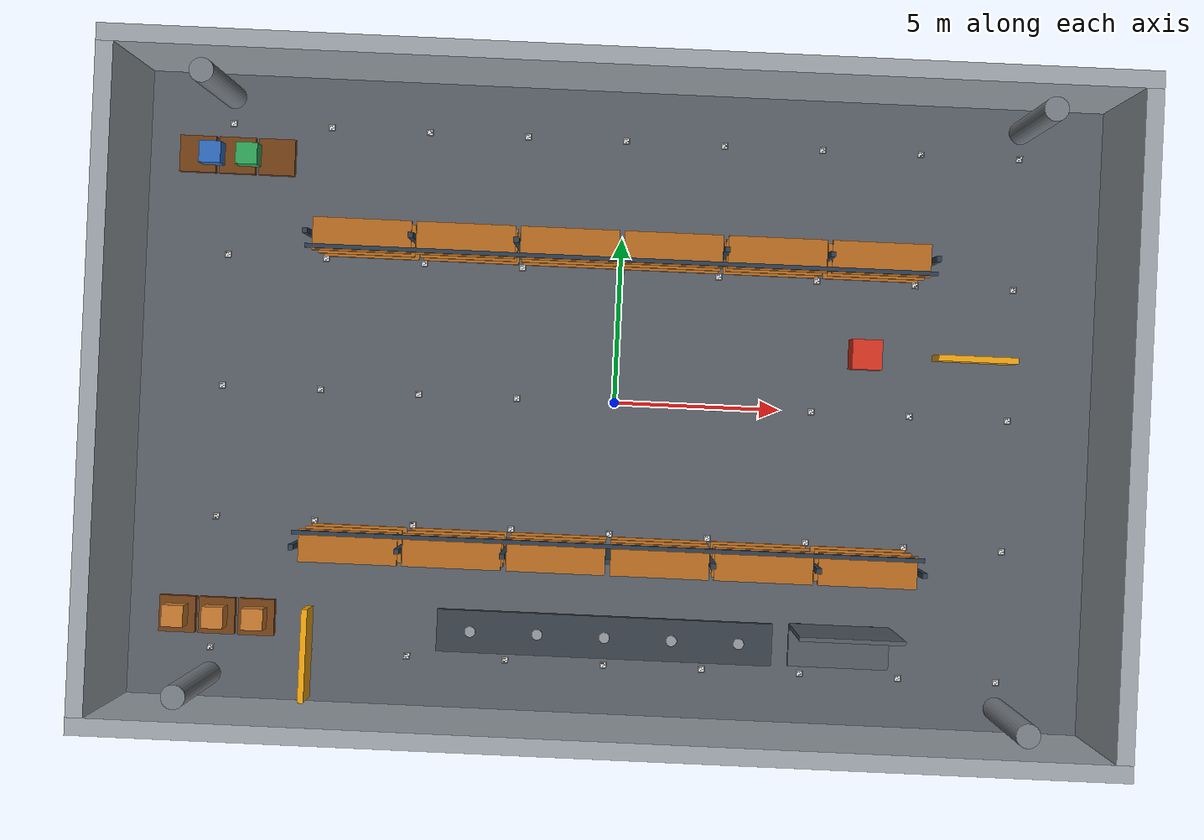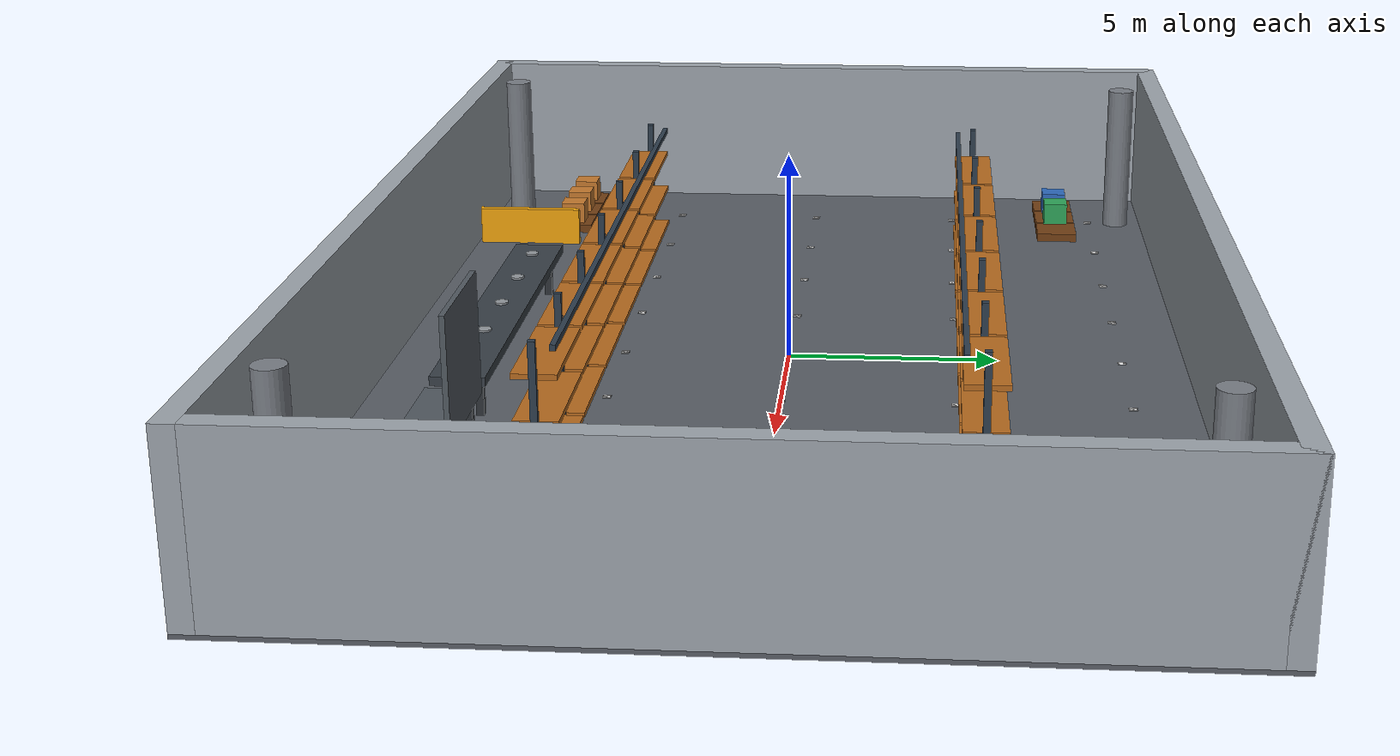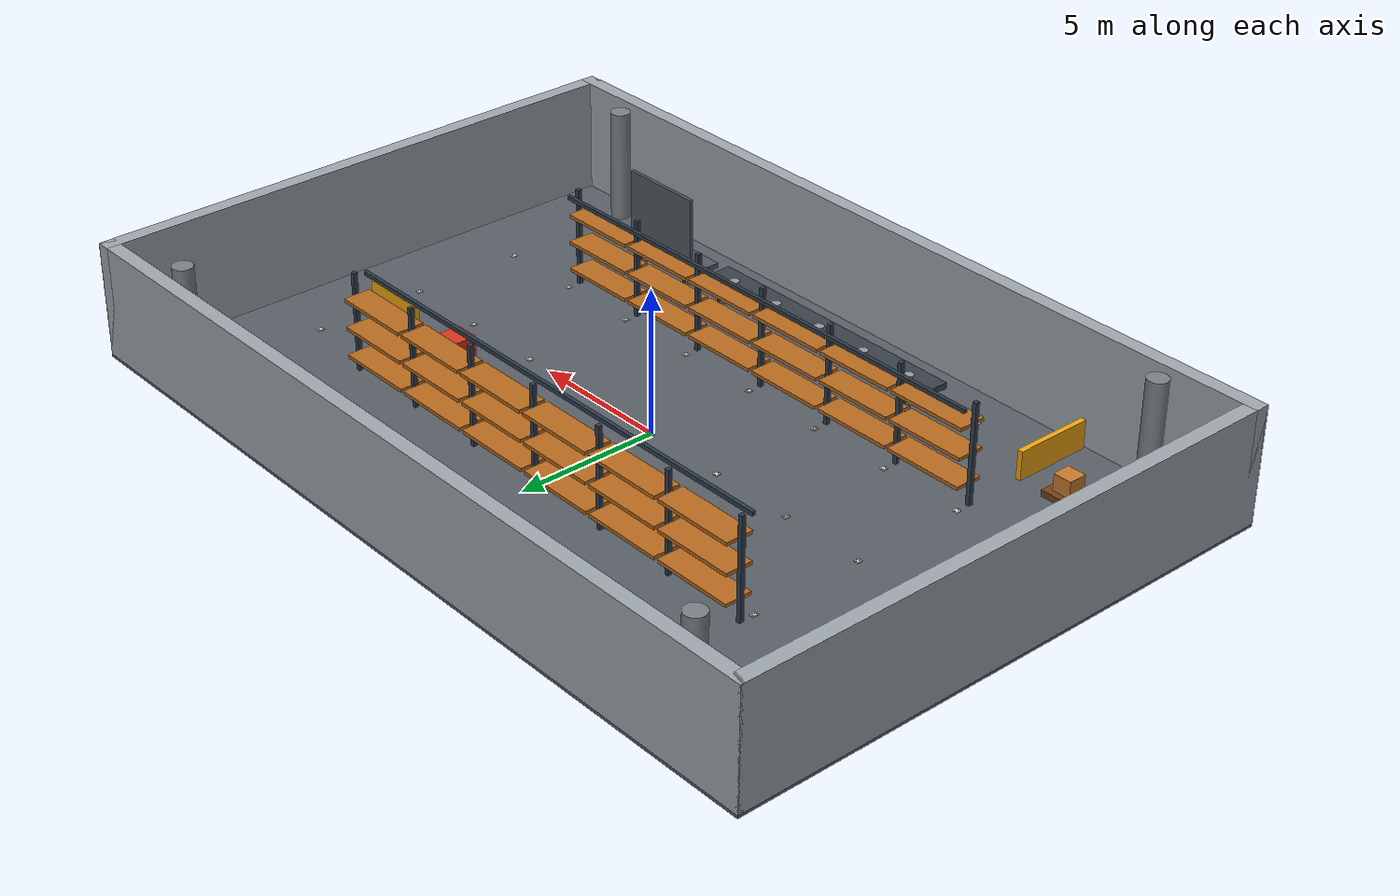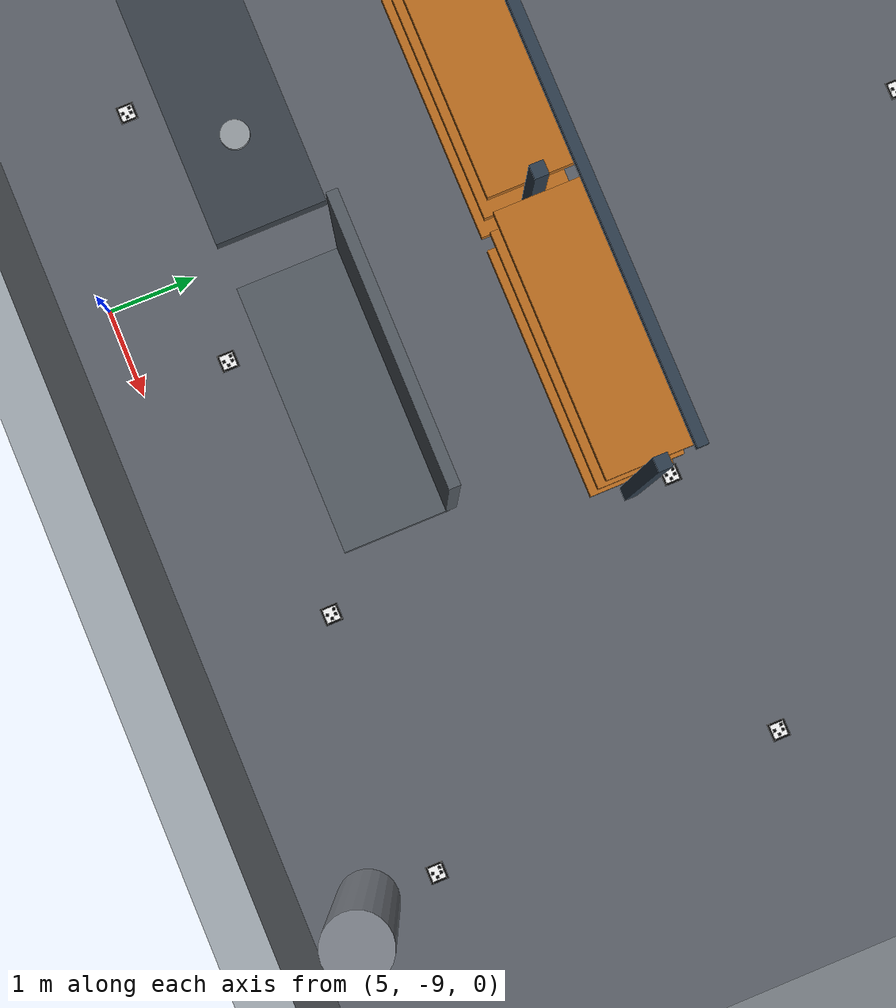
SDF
<?xml version="1.0" ?>
<sdf version="1.6">
  <!-- Phase 7 warehouse. Coordinate convention:
       Gazebo world = ROS map = WareTwin (x, y, z) origin at warehouse center.
       ROS REP-103: +X east/aisle direction, +Y north/left, +Z up. -->
  <world name="warehouse">
    <gravity>0 0 -9.81</gravity>
    <physics type="ode">
      <max_step_size>0.001</max_step_size>
      <real_time_update_rate>1000</real_time_update_rate>
      <real_time_factor>1.0</real_time_factor>
      <ode>
        <solver><type>quick</type><iters>120</iters><sor>1.3</sor></solver>
        <constraints>
          <cfm>0.0</cfm><erp>0.2</erp>
          <contact_max_correcting_vel>0.5</contact_max_correcting_vel>
          <contact_surface_layer>0.0005</contact_surface_layer>
        </constraints>
      </ode>
    </physics>
    <scene>
      <ambient>0.45 0.45 0.45 1</ambient>
      <background>0.70 0.72 0.75 1</background>
      <shadows>true</shadows>
    </scene>
    <include><uri>model://sun</uri></include>
    <plugin name="gazebo_ros_state" filename="libgazebo_ros_state.so"/>
    <!-- Diagnostic API only: exposes GetJointProperties for passive caster
         joints, which are correctly absent from ros2_control /joint_states. -->
    <plugin name="gazebo_ros_properties" filename="libgazebo_ros_properties.so"/>

    <!-- 30 m x 20 m floor; wall envelope is x=[-15,15], y=[-10,10]. -->
    <model name="floor">
      <static>true</static>
      <pose>0 0 -0.05 0 0 0</pose>
      <link name="link">
        <visual name="visual"><geometry><box><size>30 20 0.1</size></box></geometry><material><ambient>0.35 0.37 0.40 1</ambient><diffuse>0.35 0.37 0.40 1</diffuse><specular>0.1 0.1 0.1 1</specular></material></visual>
        <collision name="collision"><geometry><box><size>30 20 0.1</size></box></geometry><surface><friction><ode><mu>2.0</mu><mu2>2.0</mu2></ode></friction><contact><ode><kp>1000000</kp><kd>100</kd><max_vel>0.05</max_vel><min_depth>0</min_depth></ode></contact></surface></collision>
      </link>
    </model>
    <model name="north_wall">
      <static>true</static>
      <pose>0 9.75 2 0 0 0</pose>
      <link name="link">
        <visual name="visual"><geometry><box><size>30 0.5 4</size></box></geometry><material><ambient>0.62 0.65 0.68 1</ambient><diffuse>0.62 0.65 0.68 1</diffuse><specular>0.1 0.1 0.1 1</specular></material></visual>
        <collision name="collision"><geometry><box><size>30 0.5 4</size></box></geometry><surface><friction><ode><mu>0.8</mu><mu2>0.8</mu2></ode></friction><contact><ode><kp>1000000</kp><kd>100</kd><max_vel>0.05</max_vel><min_depth>0</min_depth></ode></contact></surface></collision>
      </link>
    </model>
    <model name="south_wall">
      <static>true</static>
      <pose>0 -9.75 2 0 0 0</pose>
      <link name="link">
        <visual name="visual"><geometry><box><size>30 0.5 4</size></box></geometry><material><ambient>0.62 0.65 0.68 1</ambient><diffuse>0.62 0.65 0.68 1</diffuse><specular>0.1 0.1 0.1 1</specular></material></visual>
        <collision name="collision"><geometry><box><size>30 0.5 4</size></box></geometry><surface><friction><ode><mu>0.8</mu><mu2>0.8</mu2></ode></friction><contact><ode><kp>1000000</kp><kd>100</kd><max_vel>0.05</max_vel><min_depth>0</min_depth></ode></contact></surface></collision>
      </link>
    </model>
    <model name="west_wall">
      <static>true</static>
      <pose>-14.75 0 2 0 0 0</pose>
      <link name="link">
        <visual name="visual"><geometry><box><size>0.5 20 4</size></box></geometry><material><ambient>0.62 0.65 0.68 1</ambient><diffuse>0.62 0.65 0.68 1</diffuse><specular>0.1 0.1 0.1 1</specular></material></visual>
        <collision name="collision"><geometry><box><size>0.5 20 4</size></box></geometry><surface><friction><ode><mu>0.8</mu><mu2>0.8</mu2></ode></friction><contact><ode><kp>1000000</kp><kd>100</kd><max_vel>0.05</max_vel><min_depth>0</min_depth></ode></contact></surface></collision>
      </link>
    </model>
    <model name="east_wall">
      <static>true</static>
      <pose>14.75 0 2 0 0 0</pose>
      <link name="link">
        <visual name="visual"><geometry><box><size>0.5 20 4</size></box></geometry><material><ambient>0.62 0.65 0.68 1</ambient><diffuse>0.62 0.65 0.68 1</diffuse><specular>0.1 0.1 0.1 1</specular></material></visual>
        <collision name="collision"><geometry><box><size>0.5 20 4</size></box></geometry><surface><friction><ode><mu>0.8</mu><mu2>0.8</mu2></ode></friction><contact><ode><kp>1000000</kp><kd>100</kd><max_vel>0.05</max_vel><min_depth>0</min_depth></ode></contact></surface></collision>
      </link>
    </model>
    <model name="pillar_nw">
      <static>true</static>
      <pose>-12 8.8 2 0 0 0</pose>
      <link name="link">
        <visual name="visual"><geometry><cylinder><radius>0.35</radius><length>4</length></cylinder></geometry><material><ambient>0.48 0.50 0.53 1</ambient><diffuse>0.48 0.50 0.53 1</diffuse><specular>0.1 0.1 0.1 1</specular></material></visual>
        <collision name="collision"><geometry><cylinder><radius>0.35</radius><length>4</length></cylinder></geometry><surface><friction><ode><mu>0.8</mu><mu2>0.8</mu2></ode></friction><contact><ode><kp>1000000</kp><kd>100</kd><max_vel>0.05</max_vel><min_depth>0</min_depth></ode></contact></surface></collision>
      </link>
    </model>
    <model name="pillar_ne">
      <static>true</static>
      <pose>12 8.8 2 0 0 0</pose>
      <link name="link">
        <visual name="visual"><geometry><cylinder><radius>0.35</radius><length>4</length></cylinder></geometry><material><ambient>0.48 0.50 0.53 1</ambient><diffuse>0.48 0.50 0.53 1</diffuse><specular>0.1 0.1 0.1 1</specular></material></visual>
        <collision name="collision"><geometry><cylinder><radius>0.35</radius><length>4</length></cylinder></geometry><surface><friction><ode><mu>0.8</mu><mu2>0.8</mu2></ode></friction><contact><ode><kp>1000000</kp><kd>100</kd><max_vel>0.05</max_vel><min_depth>0</min_depth></ode></contact></surface></collision>
      </link>
    </model>
    <model name="pillar_sw">
      <static>true</static>
      <pose>-12 -8.8 2 0 0 0</pose>
      <link name="link">
        <visual name="visual"><geometry><cylinder><radius>0.35</radius><length>4</length></cylinder></geometry><material><ambient>0.48 0.50 0.53 1</ambient><diffuse>0.48 0.50 0.53 1</diffuse><specular>0.1 0.1 0.1 1</specular></material></visual>
        <collision name="collision"><geometry><cylinder><radius>0.35</radius><length>4</length></cylinder></geometry><surface><friction><ode><mu>0.8</mu><mu2>0.8</mu2></ode></friction><contact><ode><kp>1000000</kp><kd>100</kd><max_vel>0.05</max_vel><min_depth>0</min_depth></ode></contact></surface></collision>
      </link>
    </model>
    <model name="pillar_se">
      <static>true</static>
      <pose>12 -8.8 2 0 0 0</pose>
      <link name="link">
        <visual name="visual"><geometry><cylinder><radius>0.35</radius><length>4</length></cylinder></geometry><material><ambient>0.48 0.50 0.53 1</ambient><diffuse>0.48 0.50 0.53 1</diffuse><specular>0.1 0.1 0.1 1</specular></material></visual>
        <collision name="collision"><geometry><cylinder><radius>0.35</radius><length>4</length></cylinder></geometry><surface><friction><ode><mu>0.8</mu><mu2>0.8</mu2></ode></friction><contact><ode><kp>1000000</kp><kd>100</kd><max_vel>0.05</max_vel><min_depth>0</min_depth></ode></contact></surface></collision>
      </link>
    </model>
    <model name="rack_south_post_m9">
      <static>true</static>
      <pose>-9 -4.5 1.75 0 0 0</pose>
      <link name="link">
        <visual name="visual"><geometry><box><size>0.15 0.15 3.5</size></box></geometry><material><ambient>0.18 0.24 0.30 1</ambient><diffuse>0.18 0.24 0.30 1</diffuse><specular>0.1 0.1 0.1 1</specular></material></visual>
        <collision name="collision"><geometry><box><size>0.15 0.15 3.5</size></box></geometry><surface><friction><ode><mu>0.8</mu><mu2>0.8</mu2></ode></friction><contact><ode><kp>1000000</kp><kd>100</kd><max_vel>0.05</max_vel><min_depth>0</min_depth></ode></contact></surface></collision>
      </link>
    </model>
    <model name="rack_south_post_m6">
      <static>true</static>
      <pose>-6 -4.5 1.75 0 0 0</pose>
      <link name="link">
        <visual name="visual"><geometry><box><size>0.15 0.15 3.5</size></box></geometry><material><ambient>0.18 0.24 0.30 1</ambient><diffuse>0.18 0.24 0.30 1</diffuse><specular>0.1 0.1 0.1 1</specular></material></visual>
        <collision name="collision"><geometry><box><size>0.15 0.15 3.5</size></box></geometry><surface><friction><ode><mu>0.8</mu><mu2>0.8</mu2></ode></friction><contact><ode><kp>1000000</kp><kd>100</kd><max_vel>0.05</max_vel><min_depth>0</min_depth></ode></contact></surface></collision>
      </link>
    </model>
    <model name="rack_south_post_m3">
      <static>true</static>
      <pose>-3 -4.5 1.75 0 0 0</pose>
      <link name="link">
        <visual name="visual"><geometry><box><size>0.15 0.15 3.5</size></box></geometry><material><ambient>0.18 0.24 0.30 1</ambient><diffuse>0.18 0.24 0.30 1</diffuse><specular>0.1 0.1 0.1 1</specular></material></visual>
        <collision name="collision"><geometry><box><size>0.15 0.15 3.5</size></box></geometry><surface><friction><ode><mu>0.8</mu><mu2>0.8</mu2></ode></friction><contact><ode><kp>1000000</kp><kd>100</kd><max_vel>0.05</max_vel><min_depth>0</min_depth></ode></contact></surface></collision>
      </link>
    </model>
    <model name="rack_south_post_0">
      <static>true</static>
      <pose>0 -4.5 1.75 0 0 0</pose>
      <link name="link">
        <visual name="visual"><geometry><box><size>0.15 0.15 3.5</size></box></geometry><material><ambient>0.18 0.24 0.30 1</ambient><diffuse>0.18 0.24 0.30 1</diffuse><specular>0.1 0.1 0.1 1</specular></material></visual>
        <collision name="collision"><geometry><box><size>0.15 0.15 3.5</size></box></geometry><surface><friction><ode><mu>0.8</mu><mu2>0.8</mu2></ode></friction><contact><ode><kp>1000000</kp><kd>100</kd><max_vel>0.05</max_vel><min_depth>0</min_depth></ode></contact></surface></collision>
      </link>
    </model>
    <model name="rack_south_post_3">
      <static>true</static>
      <pose>3 -4.5 1.75 0 0 0</pose>
      <link name="link">
        <visual name="visual"><geometry><box><size>0.15 0.15 3.5</size></box></geometry><material><ambient>0.18 0.24 0.30 1</ambient><diffuse>0.18 0.24 0.30 1</diffuse><specular>0.1 0.1 0.1 1</specular></material></visual>
        <collision name="collision"><geometry><box><size>0.15 0.15 3.5</size></box></geometry><surface><friction><ode><mu>0.8</mu><mu2>0.8</mu2></ode></friction><contact><ode><kp>1000000</kp><kd>100</kd><max_vel>0.05</max_vel><min_depth>0</min_depth></ode></contact></surface></collision>
      </link>
    </model>
    <model name="rack_south_post_6">
      <static>true</static>
      <pose>6 -4.5 1.75 0 0 0</pose>
      <link name="link">
        <visual name="visual"><geometry><box><size>0.15 0.15 3.5</size></box></geometry><material><ambient>0.18 0.24 0.30 1</ambient><diffuse>0.18 0.24 0.30 1</diffuse><specular>0.1 0.1 0.1 1</specular></material></visual>
        <collision name="collision"><geometry><box><size>0.15 0.15 3.5</size></box></geometry><surface><friction><ode><mu>0.8</mu><mu2>0.8</mu2></ode></friction><contact><ode><kp>1000000</kp><kd>100</kd><max_vel>0.05</max_vel><min_depth>0</min_depth></ode></contact></surface></collision>
      </link>
    </model>
    <model name="rack_south_post_9">
      <static>true</static>
      <pose>9 -4.5 1.75 0 0 0</pose>
      <link name="link">
        <visual name="visual"><geometry><box><size>0.15 0.15 3.5</size></box></geometry><material><ambient>0.18 0.24 0.30 1</ambient><diffuse>0.18 0.24 0.30 1</diffuse><specular>0.1 0.1 0.1 1</specular></material></visual>
        <collision name="collision"><geometry><box><size>0.15 0.15 3.5</size></box></geometry><surface><friction><ode><mu>0.8</mu><mu2>0.8</mu2></ode></friction><contact><ode><kp>1000000</kp><kd>100</kd><max_vel>0.05</max_vel><min_depth>0</min_depth></ode></contact></surface></collision>
      </link>
    </model>
    <model name="rack_south_shelf_m7.5_low">
      <static>true</static>
      <pose>-7.5 -4.5 0.7 0 0 0</pose>
      <link name="link">
        <visual name="visual"><geometry><box><size>2.85 0.95 0.12</size></box></geometry><material><ambient>0.72 0.42 0.12 1</ambient><diffuse>0.72 0.42 0.12 1</diffuse><specular>0.1 0.1 0.1 1</specular></material></visual>
        <collision name="collision"><geometry><box><size>2.85 0.95 0.12</size></box></geometry><surface><friction><ode><mu>0.8</mu><mu2>0.8</mu2></ode></friction><contact><ode><kp>1000000</kp><kd>100</kd><max_vel>0.05</max_vel><min_depth>0</min_depth></ode></contact></surface></collision>
      </link>
    </model>
    <model name="rack_south_shelf_m7.5_mid">
      <static>true</static>
      <pose>-7.5 -4.5 1.7 0 0 0</pose>
      <link name="link">
        <visual name="visual"><geometry><box><size>2.85 0.95 0.12</size></box></geometry><material><ambient>0.72 0.42 0.12 1</ambient><diffuse>0.72 0.42 0.12 1</diffuse><specular>0.1 0.1 0.1 1</specular></material></visual>
        <collision name="collision"><geometry><box><size>2.85 0.95 0.12</size></box></geometry><surface><friction><ode><mu>0.8</mu><mu2>0.8</mu2></ode></friction><contact><ode><kp>1000000</kp><kd>100</kd><max_vel>0.05</max_vel><min_depth>0</min_depth></ode></contact></surface></collision>
      </link>
    </model>
    <model name="rack_south_shelf_m7.5_high">
      <static>true</static>
      <pose>-7.5 -4.5 2.7 0 0 0</pose>
      <link name="link">
        <visual name="visual"><geometry><box><size>2.85 0.95 0.12</size></box></geometry><material><ambient>0.72 0.42 0.12 1</ambient><diffuse>0.72 0.42 0.12 1</diffuse><specular>0.1 0.1 0.1 1</specular></material></visual>
        <collision name="collision"><geometry><box><size>2.85 0.95 0.12</size></box></geometry><surface><friction><ode><mu>0.8</mu><mu2>0.8</mu2></ode></friction><contact><ode><kp>1000000</kp><kd>100</kd><max_vel>0.05</max_vel><min_depth>0</min_depth></ode></contact></surface></collision>
      </link>
    </model>
    <model name="rack_south_shelf_m4.5_low">
      <static>true</static>
      <pose>-4.5 -4.5 0.7 0 0 0</pose>
      <link name="link">
        <visual name="visual"><geometry><box><size>2.85 0.95 0.12</size></box></geometry><material><ambient>0.72 0.42 0.12 1</ambient><diffuse>0.72 0.42 0.12 1</diffuse><specular>0.1 0.1 0.1 1</specular></material></visual>
        <collision name="collision"><geometry><box><size>2.85 0.95 0.12</size></box></geometry><surface><friction><ode><mu>0.8</mu><mu2>0.8</mu2></ode></friction><contact><ode><kp>1000000</kp><kd>100</kd><max_vel>0.05</max_vel><min_depth>0</min_depth></ode></contact></surface></collision>
      </link>
    </model>
    <model name="rack_south_shelf_m4.5_mid">
      <static>true</static>
      <pose>-4.5 -4.5 1.7 0 0 0</pose>
      <link name="link">
        <visual name="visual"><geometry><box><size>2.85 0.95 0.12</size></box></geometry><material><ambient>0.72 0.42 0.12 1</ambient><diffuse>0.72 0.42 0.12 1</diffuse><specular>0.1 0.1 0.1 1</specular></material></visual>
        <collision name="collision"><geometry><box><size>2.85 0.95 0.12</size></box></geometry><surface><friction><ode><mu>0.8</mu><mu2>0.8</mu2></ode></friction><contact><ode><kp>1000000</kp><kd>100</kd><max_vel>0.05</max_vel><min_depth>0</min_depth></ode></contact></surface></collision>
      </link>
    </model>
    <model name="rack_south_shelf_m4.5_high">
      <static>true</static>
      <pose>-4.5 -4.5 2.7 0 0 0</pose>
      <link name="link">
        <visual name="visual"><geometry><box><size>2.85 0.95 0.12</size></box></geometry><material><ambient>0.72 0.42 0.12 1</ambient><diffuse>0.72 0.42 0.12 1</diffuse><specular>0.1 0.1 0.1 1</specular></material></visual>
        <collision name="collision"><geometry><box><size>2.85 0.95 0.12</size></box></geometry><surface><friction><ode><mu>0.8</mu><mu2>0.8</mu2></ode></friction><contact><ode><kp>1000000</kp><kd>100</kd><max_vel>0.05</max_vel><min_depth>0</min_depth></ode></contact></surface></collision>
      </link>
    </model>
    <model name="rack_south_shelf_m1.5_low">
      <static>true</static>
      <pose>-1.5 -4.5 0.7 0 0 0</pose>
      <link name="link">
        <visual name="visual"><geometry><box><size>2.85 0.95 0.12</size></box></geometry><material><ambient>0.72 0.42 0.12 1</ambient><diffuse>0.72 0.42 0.12 1</diffuse><specular>0.1 0.1 0.1 1</specular></material></visual>
        <collision name="collision"><geometry><box><size>2.85 0.95 0.12</size></box></geometry><surface><friction><ode><mu>0.8</mu><mu2>0.8</mu2></ode></friction><contact><ode><kp>1000000</kp><kd>100</kd><max_vel>0.05</max_vel><min_depth>0</min_depth></ode></contact></surface></collision>
      </link>
    </model>
    <model name="rack_south_shelf_m1.5_mid">
      <static>true</static>
      <pose>-1.5 -4.5 1.7 0 0 0</pose>
      <link name="link">
        <visual name="visual"><geometry><box><size>2.85 0.95 0.12</size></box></geometry><material><ambient>0.72 0.42 0.12 1</ambient><diffuse>0.72 0.42 0.12 1</diffuse><specular>0.1 0.1 0.1 1</specular></material></visual>
        <collision name="collision"><geometry><box><size>2.85 0.95 0.12</size></box></geometry><surface><friction><ode><mu>0.8</mu><mu2>0.8</mu2></ode></friction><contact><ode><kp>1000000</kp><kd>100</kd><max_vel>0.05</max_vel><min_depth>0</min_depth></ode></contact></surface></collision>
      </link>
    </model>
    <model name="rack_south_shelf_m1.5_high">
      <static>true</static>
      <pose>-1.5 -4.5 2.7 0 0 0</pose>
      <link name="link">
        <visual name="visual"><geometry><box><size>2.85 0.95 0.12</size></box></geometry><material><ambient>0.72 0.42 0.12 1</ambient><diffuse>0.72 0.42 0.12 1</diffuse><specular>0.1 0.1 0.1 1</specular></material></visual>
        <collision name="collision"><geometry><box><size>2.85 0.95 0.12</size></box></geometry><surface><friction><ode><mu>0.8</mu><mu2>0.8</mu2></ode></friction><contact><ode><kp>1000000</kp><kd>100</kd><max_vel>0.05</max_vel><min_depth>0</min_depth></ode></contact></surface></collision>
      </link>
    </model>
    <model name="rack_south_shelf_1.5_low">
      <static>true</static>
      <pose>1.5 -4.5 0.7 0 0 0</pose>
      <link name="link">
        <visual name="visual"><geometry><box><size>2.85 0.95 0.12</size></box></geometry><material><ambient>0.72 0.42 0.12 1</ambient><diffuse>0.72 0.42 0.12 1</diffuse><specular>0.1 0.1 0.1 1</specular></material></visual>
        <collision name="collision"><geometry><box><size>2.85 0.95 0.12</size></box></geometry><surface><friction><ode><mu>0.8</mu><mu2>0.8</mu2></ode></friction><contact><ode><kp>1000000</kp><kd>100</kd><max_vel>0.05</max_vel><min_depth>0</min_depth></ode></contact></surface></collision>
      </link>
    </model>
    <model name="rack_south_shelf_1.5_mid">
      <static>true</static>
      <pose>1.5 -4.5 1.7 0 0 0</pose>
      <link name="link">
        <visual name="visual"><geometry><box><size>2.85 0.95 0.12</size></box></geometry><material><ambient>0.72 0.42 0.12 1</ambient><diffuse>0.72 0.42 0.12 1</diffuse><specular>0.1 0.1 0.1 1</specular></material></visual>
        <collision name="collision"><geometry><box><size>2.85 0.95 0.12</size></box></geometry><surface><friction><ode><mu>0.8</mu><mu2>0.8</mu2></ode></friction><contact><ode><kp>1000000</kp><kd>100</kd><max_vel>0.05</max_vel><min_depth>0</min_depth></ode></contact></surface></collision>
      </link>
    </model>
    <model name="rack_south_shelf_1.5_high">
      <static>true</static>
      <pose>1.5 -4.5 2.7 0 0 0</pose>
      <link name="link">
        <visual name="visual"><geometry><box><size>2.85 0.95 0.12</size></box></geometry><material><ambient>0.72 0.42 0.12 1</ambient><diffuse>0.72 0.42 0.12 1</diffuse><specular>0.1 0.1 0.1 1</specular></material></visual>
        <collision name="collision"><geometry><box><size>2.85 0.95 0.12</size></box></geometry><surface><friction><ode><mu>0.8</mu><mu2>0.8</mu2></ode></friction><contact><ode><kp>1000000</kp><kd>100</kd><max_vel>0.05</max_vel><min_depth>0</min_depth></ode></contact></surface></collision>
      </link>
    </model>
    <model name="rack_south_shelf_4.5_low">
      <static>true</static>
      <pose>4.5 -4.5 0.7 0 0 0</pose>
      <link name="link">
        <visual name="visual"><geometry><box><size>2.85 0.95 0.12</size></box></geometry><material><ambient>0.72 0.42 0.12 1</ambient><diffuse>0.72 0.42 0.12 1</diffuse><specular>0.1 0.1 0.1 1</specular></material></visual>
        <collision name="collision"><geometry><box><size>2.85 0.95 0.12</size></box></geometry><surface><friction><ode><mu>0.8</mu><mu2>0.8</mu2></ode></friction><contact><ode><kp>1000000</kp><kd>100</kd><max_vel>0.05</max_vel><min_depth>0</min_depth></ode></contact></surface></collision>
      </link>
    </model>
    <model name="rack_south_shelf_4.5_mid">
      <static>true</static>
      <pose>4.5 -4.5 1.7 0 0 0</pose>
      <link name="link">
        <visual name="visual"><geometry><box><size>2.85 0.95 0.12</size></box></geometry><material><ambient>0.72 0.42 0.12 1</ambient><diffuse>0.72 0.42 0.12 1</diffuse><specular>0.1 0.1 0.1 1</specular></material></visual>
        <collision name="collision"><geometry><box><size>2.85 0.95 0.12</size></box></geometry><surface><friction><ode><mu>0.8</mu><mu2>0.8</mu2></ode></friction><contact><ode><kp>1000000</kp><kd>100</kd><max_vel>0.05</max_vel><min_depth>0</min_depth></ode></contact></surface></collision>
      </link>
    </model>
    <model name="rack_south_shelf_4.5_high">
      <static>true</static>
      <pose>4.5 -4.5 2.7 0 0 0</pose>
      <link name="link">
        <visual name="visual"><geometry><box><size>2.85 0.95 0.12</size></box></geometry><material><ambient>0.72 0.42 0.12 1</ambient><diffuse>0.72 0.42 0.12 1</diffuse><specular>0.1 0.1 0.1 1</specular></material></visual>
        <collision name="collision"><geometry><box><size>2.85 0.95 0.12</size></box></geometry><surface><friction><ode><mu>0.8</mu><mu2>0.8</mu2></ode></friction><contact><ode><kp>1000000</kp><kd>100</kd><max_vel>0.05</max_vel><min_depth>0</min_depth></ode></contact></surface></collision>
      </link>
    </model>
    <model name="rack_south_shelf_7.5_low">
      <static>true</static>
      <pose>7.5 -4.5 0.7 0 0 0</pose>
      <link name="link">
        <visual name="visual"><geometry><box><size>2.85 0.95 0.12</size></box></geometry><material><ambient>0.72 0.42 0.12 1</ambient><diffuse>0.72 0.42 0.12 1</diffuse><specular>0.1 0.1 0.1 1</specular></material></visual>
        <collision name="collision"><geometry><box><size>2.85 0.95 0.12</size></box></geometry><surface><friction><ode><mu>0.8</mu><mu2>0.8</mu2></ode></friction><contact><ode><kp>1000000</kp><kd>100</kd><max_vel>0.05</max_vel><min_depth>0</min_depth></ode></contact></surface></collision>
      </link>
    </model>
    <model name="rack_south_shelf_7.5_mid">
      <static>true</static>
      <pose>7.5 -4.5 1.7 0 0 0</pose>
      <link name="link">
        <visual name="visual"><geometry><box><size>2.85 0.95 0.12</size></box></geometry><material><ambient>0.72 0.42 0.12 1</ambient><diffuse>0.72 0.42 0.12 1</diffuse><specular>0.1 0.1 0.1 1</specular></material></visual>
        <collision name="collision"><geometry><box><size>2.85 0.95 0.12</size></box></geometry><surface><friction><ode><mu>0.8</mu><mu2>0.8</mu2></ode></friction><contact><ode><kp>1000000</kp><kd>100</kd><max_vel>0.05</max_vel><min_depth>0</min_depth></ode></contact></surface></collision>
      </link>
    </model>
    <model name="rack_south_shelf_7.5_high">
      <static>true</static>
      <pose>7.5 -4.5 2.7 0 0 0</pose>
      <link name="link">
        <visual name="visual"><geometry><box><size>2.85 0.95 0.12</size></box></geometry><material><ambient>0.72 0.42 0.12 1</ambient><diffuse>0.72 0.42 0.12 1</diffuse><specular>0.1 0.1 0.1 1</specular></material></visual>
        <collision name="collision"><geometry><box><size>2.85 0.95 0.12</size></box></geometry><surface><friction><ode><mu>0.8</mu><mu2>0.8</mu2></ode></friction><contact><ode><kp>1000000</kp><kd>100</kd><max_vel>0.05</max_vel><min_depth>0</min_depth></ode></contact></surface></collision>
      </link>
    </model>
    <model name="rack_south_back_beam">
      <static>true</static>
      <pose>0 -4.08 3.35 0 0 0</pose>
      <link name="link">
        <visual name="visual"><geometry><box><size>18 0.12 0.14</size></box></geometry><material><ambient>0.18 0.24 0.30 1</ambient><diffuse>0.18 0.24 0.30 1</diffuse><specular>0.1 0.1 0.1 1</specular></material></visual>
        <collision name="collision"><geometry><box><size>18 0.12 0.14</size></box></geometry><surface><friction><ode><mu>0.8</mu><mu2>0.8</mu2></ode></friction><contact><ode><kp>1000000</kp><kd>100</kd><max_vel>0.05</max_vel><min_depth>0</min_depth></ode></contact></surface></collision>
      </link>
    </model>
    <model name="rack_north_post_m9">
      <static>true</static>
      <pose>-9 4.5 1.75 0 0 0</pose>
      <link name="link">
        <visual name="visual"><geometry><box><size>0.15 0.15 3.5</size></box></geometry><material><ambient>0.18 0.24 0.30 1</ambient><diffuse>0.18 0.24 0.30 1</diffuse><specular>0.1 0.1 0.1 1</specular></material></visual>
        <collision name="collision"><geometry><box><size>0.15 0.15 3.5</size></box></geometry><surface><friction><ode><mu>0.8</mu><mu2>0.8</mu2></ode></friction><contact><ode><kp>1000000</kp><kd>100</kd><max_vel>0.05</max_vel><min_depth>0</min_depth></ode></contact></surface></collision>
      </link>
    </model>
    <model name="rack_north_post_m6">
      <static>true</static>
      <pose>-6 4.5 1.75 0 0 0</pose>
      <link name="link">
        <visual name="visual"><geometry><box><size>0.15 0.15 3.5</size></box></geometry><material><ambient>0.18 0.24 0.30 1</ambient><diffuse>0.18 0.24 0.30 1</diffuse><specular>0.1 0.1 0.1 1</specular></material></visual>
        <collision name="collision"><geometry><box><size>0.15 0.15 3.5</size></box></geometry><surface><friction><ode><mu>0.8</mu><mu2>0.8</mu2></ode></friction><contact><ode><kp>1000000</kp><kd>100</kd><max_vel>0.05</max_vel><min_depth>0</min_depth></ode></contact></surface></collision>
      </link>
    </model>
    <model name="rack_north_post_m3">
      <static>true</static>
      <pose>-3 4.5 1.75 0 0 0</pose>
      <link name="link">
        <visual name="visual"><geometry><box><size>0.15 0.15 3.5</size></box></geometry><material><ambient>0.18 0.24 0.30 1</ambient><diffuse>0.18 0.24 0.30 1</diffuse><specular>0.1 0.1 0.1 1</specular></material></visual>
        <collision name="collision"><geometry><box><size>0.15 0.15 3.5</size></box></geometry><surface><friction><ode><mu>0.8</mu><mu2>0.8</mu2></ode></friction><contact><ode><kp>1000000</kp><kd>100</kd><max_vel>0.05</max_vel><min_depth>0</min_depth></ode></contact></surface></collision>
      </link>
    </model>
    <model name="rack_north_post_0">
      <static>true</static>
      <pose>0 4.5 1.75 0 0 0</pose>
      <link name="link">
        <visual name="visual"><geometry><box><size>0.15 0.15 3.5</size></box></geometry><material><ambient>0.18 0.24 0.30 1</ambient><diffuse>0.18 0.24 0.30 1</diffuse><specular>0.1 0.1 0.1 1</specular></material></visual>
        <collision name="collision"><geometry><box><size>0.15 0.15 3.5</size></box></geometry><surface><friction><ode><mu>0.8</mu><mu2>0.8</mu2></ode></friction><contact><ode><kp>1000000</kp><kd>100</kd><max_vel>0.05</max_vel><min_depth>0</min_depth></ode></contact></surface></collision>
      </link>
    </model>
    <model name="rack_north_post_3">
      <static>true</static>
      <pose>3 4.5 1.75 0 0 0</pose>
      <link name="link">
        <visual name="visual"><geometry><box><size>0.15 0.15 3.5</size></box></geometry><material><ambient>0.18 0.24 0.30 1</ambient><diffuse>0.18 0.24 0.30 1</diffuse><specular>0.1 0.1 0.1 1</specular></material></visual>
        <collision name="collision"><geometry><box><size>0.15 0.15 3.5</size></box></geometry><surface><friction><ode><mu>0.8</mu><mu2>0.8</mu2></ode></friction><contact><ode><kp>1000000</kp><kd>100</kd><max_vel>0.05</max_vel><min_depth>0</min_depth></ode></contact></surface></collision>
      </link>
    </model>
    <model name="rack_north_post_6">
      <static>true</static>
      <pose>6 4.5 1.75 0 0 0</pose>
      <link name="link">
        <visual name="visual"><geometry><box><size>0.15 0.15 3.5</size></box></geometry><material><ambient>0.18 0.24 0.30 1</ambient><diffuse>0.18 0.24 0.30 1</diffuse><specular>0.1 0.1 0.1 1</specular></material></visual>
        <collision name="collision"><geometry><box><size>0.15 0.15 3.5</size></box></geometry><surface><friction><ode><mu>0.8</mu><mu2>0.8</mu2></ode></friction><contact><ode><kp>1000000</kp><kd>100</kd><max_vel>0.05</max_vel><min_depth>0</min_depth></ode></contact></surface></collision>
      </link>
    </model>
    <model name="rack_north_post_9">
      <static>true</static>
      <pose>9 4.5 1.75 0 0 0</pose>
      <link name="link">
        <visual name="visual"><geometry><box><size>0.15 0.15 3.5</size></box></geometry><material><ambient>0.18 0.24 0.30 1</ambient><diffuse>0.18 0.24 0.30 1</diffuse><specular>0.1 0.1 0.1 1</specular></material></visual>
        <collision name="collision"><geometry><box><size>0.15 0.15 3.5</size></box></geometry><surface><friction><ode><mu>0.8</mu><mu2>0.8</mu2></ode></friction><contact><ode><kp>1000000</kp><kd>100</kd><max_vel>0.05</max_vel><min_depth>0</min_depth></ode></contact></surface></collision>
      </link>
    </model>
    <model name="rack_north_shelf_m7.5_low">
      <static>true</static>
      <pose>-7.5 4.5 0.7 0 0 0</pose>
      <link name="link">
        <visual name="visual"><geometry><box><size>2.85 0.95 0.12</size></box></geometry><material><ambient>0.72 0.42 0.12 1</ambient><diffuse>0.72 0.42 0.12 1</diffuse><specular>0.1 0.1 0.1 1</specular></material></visual>
        <collision name="collision"><geometry><box><size>2.85 0.95 0.12</size></box></geometry><surface><friction><ode><mu>0.8</mu><mu2>0.8</mu2></ode></friction><contact><ode><kp>1000000</kp><kd>100</kd><max_vel>0.05</max_vel><min_depth>0</min_depth></ode></contact></surface></collision>
      </link>
    </model>
    <model name="rack_north_shelf_m7.5_mid">
      <static>true</static>
      <pose>-7.5 4.5 1.7 0 0 0</pose>
      <link name="link">
        <visual name="visual"><geometry><box><size>2.85 0.95 0.12</size></box></geometry><material><ambient>0.72 0.42 0.12 1</ambient><diffuse>0.72 0.42 0.12 1</diffuse><specular>0.1 0.1 0.1 1</specular></material></visual>
        <collision name="collision"><geometry><box><size>2.85 0.95 0.12</size></box></geometry><surface><friction><ode><mu>0.8</mu><mu2>0.8</mu2></ode></friction><contact><ode><kp>1000000</kp><kd>100</kd><max_vel>0.05</max_vel><min_depth>0</min_depth></ode></contact></surface></collision>
      </link>
    </model>
    <model name="rack_north_shelf_m7.5_high">
      <static>true</static>
      <pose>-7.5 4.5 2.7 0 0 0</pose>
      <link name="link">
        <visual name="visual"><geometry><box><size>2.85 0.95 0.12</size></box></geometry><material><ambient>0.72 0.42 0.12 1</ambient><diffuse>0.72 0.42 0.12 1</diffuse><specular>0.1 0.1 0.1 1</specular></material></visual>
        <collision name="collision"><geometry><box><size>2.85 0.95 0.12</size></box></geometry><surface><friction><ode><mu>0.8</mu><mu2>0.8</mu2></ode></friction><contact><ode><kp>1000000</kp><kd>100</kd><max_vel>0.05</max_vel><min_depth>0</min_depth></ode></contact></surface></collision>
      </link>
    </model>
    <model name="rack_north_shelf_m4.5_low">
      <static>true</static>
      <pose>-4.5 4.5 0.7 0 0 0</pose>
      <link name="link">
        <visual name="visual"><geometry><box><size>2.85 0.95 0.12</size></box></geometry><material><ambient>0.72 0.42 0.12 1</ambient><diffuse>0.72 0.42 0.12 1</diffuse><specular>0.1 0.1 0.1 1</specular></material></visual>
        <collision name="collision"><geometry><box><size>2.85 0.95 0.12</size></box></geometry><surface><friction><ode><mu>0.8</mu><mu2>0.8</mu2></ode></friction><contact><ode><kp>1000000</kp><kd>100</kd><max_vel>0.05</max_vel><min_depth>0</min_depth></ode></contact></surface></collision>
      </link>
    </model>
    <model name="rack_north_shelf_m4.5_mid">
      <static>true</static>
      <pose>-4.5 4.5 1.7 0 0 0</pose>
      <link name="link">
        <visual name="visual"><geometry><box><size>2.85 0.95 0.12</size></box></geometry><material><ambient>0.72 0.42 0.12 1</ambient><diffuse>0.72 0.42 0.12 1</diffuse><specular>0.1 0.1 0.1 1</specular></material></visual>
        <collision name="collision"><geometry><box><size>2.85 0.95 0.12</size></box></geometry><surface><friction><ode><mu>0.8</mu><mu2>0.8</mu2></ode></friction><contact><ode><kp>1000000</kp><kd>100</kd><max_vel>0.05</max_vel><min_depth>0</min_depth></ode></contact></surface></collision>
      </link>
    </model>
    <model name="rack_north_shelf_m4.5_high">
      <static>true</static>
      <pose>-4.5 4.5 2.7 0 0 0</pose>
      <link name="link">
        <visual name="visual"><geometry><box><size>2.85 0.95 0.12</size></box></geometry><material><ambient>0.72 0.42 0.12 1</ambient><diffuse>0.72 0.42 0.12 1</diffuse><specular>0.1 0.1 0.1 1</specular></material></visual>
        <collision name="collision"><geometry><box><size>2.85 0.95 0.12</size></box></geometry><surface><friction><ode><mu>0.8</mu><mu2>0.8</mu2></ode></friction><contact><ode><kp>1000000</kp><kd>100</kd><max_vel>0.05</max_vel><min_depth>0</min_depth></ode></contact></surface></collision>
      </link>
    </model>
    <model name="rack_north_shelf_m1.5_low">
      <static>true</static>
      <pose>-1.5 4.5 0.7 0 0 0</pose>
      <link name="link">
        <visual name="visual"><geometry><box><size>2.85 0.95 0.12</size></box></geometry><material><ambient>0.72 0.42 0.12 1</ambient><diffuse>0.72 0.42 0.12 1</diffuse><specular>0.1 0.1 0.1 1</specular></material></visual>
        <collision name="collision"><geometry><box><size>2.85 0.95 0.12</size></box></geometry><surface><friction><ode><mu>0.8</mu><mu2>0.8</mu2></ode></friction><contact><ode><kp>1000000</kp><kd>100</kd><max_vel>0.05</max_vel><min_depth>0</min_depth></ode></contact></surface></collision>
      </link>
    </model>
    <model name="rack_north_shelf_m1.5_mid">
      <static>true</static>
      <pose>-1.5 4.5 1.7 0 0 0</pose>
      <link name="link">
        <visual name="visual"><geometry><box><size>2.85 0.95 0.12</size></box></geometry><material><ambient>0.72 0.42 0.12 1</ambient><diffuse>0.72 0.42 0.12 1</diffuse><specular>0.1 0.1 0.1 1</specular></material></visual>
        <collision name="collision"><geometry><box><size>2.85 0.95 0.12</size></box></geometry><surface><friction><ode><mu>0.8</mu><mu2>0.8</mu2></ode></friction><contact><ode><kp>1000000</kp><kd>100</kd><max_vel>0.05</max_vel><min_depth>0</min_depth></ode></contact></surface></collision>
      </link>
    </model>
    <model name="rack_north_shelf_m1.5_high">
      <static>true</static>
      <pose>-1.5 4.5 2.7 0 0 0</pose>
      <link name="link">
        <visual name="visual"><geometry><box><size>2.85 0.95 0.12</size></box></geometry><material><ambient>0.72 0.42 0.12 1</ambient><diffuse>0.72 0.42 0.12 1</diffuse><specular>0.1 0.1 0.1 1</specular></material></visual>
        <collision name="collision"><geometry><box><size>2.85 0.95 0.12</size></box></geometry><surface><friction><ode><mu>0.8</mu><mu2>0.8</mu2></ode></friction><contact><ode><kp>1000000</kp><kd>100</kd><max_vel>0.05</max_vel><min_depth>0</min_depth></ode></contact></surface></collision>
      </link>
    </model>
    <model name="rack_north_shelf_1.5_low">
      <static>true</static>
      <pose>1.5 4.5 0.7 0 0 0</pose>
      <link name="link">
        <visual name="visual"><geometry><box><size>2.85 0.95 0.12</size></box></geometry><material><ambient>0.72 0.42 0.12 1</ambient><diffuse>0.72 0.42 0.12 1</diffuse><specular>0.1 0.1 0.1 1</specular></material></visual>
        <collision name="collision"><geometry><box><size>2.85 0.95 0.12</size></box></geometry><surface><friction><ode><mu>0.8</mu><mu2>0.8</mu2></ode></friction><contact><ode><kp>1000000</kp><kd>100</kd><max_vel>0.05</max_vel><min_depth>0</min_depth></ode></contact></surface></collision>
      </link>
    </model>
    <model name="rack_north_shelf_1.5_mid">
      <static>true</static>
      <pose>1.5 4.5 1.7 0 0 0</pose>
      <link name="link">
        <visual name="visual"><geometry><box><size>2.85 0.95 0.12</size></box></geometry><material><ambient>0.72 0.42 0.12 1</ambient><diffuse>0.72 0.42 0.12 1</diffuse><specular>0.1 0.1 0.1 1</specular></material></visual>
        <collision name="collision"><geometry><box><size>2.85 0.95 0.12</size></box></geometry><surface><friction><ode><mu>0.8</mu><mu2>0.8</mu2></ode></friction><contact><ode><kp>1000000</kp><kd>100</kd><max_vel>0.05</max_vel><min_depth>0</min_depth></ode></contact></surface></collision>
      </link>
    </model>
    <model name="rack_north_shelf_1.5_high">
      <static>true</static>
      <pose>1.5 4.5 2.7 0 0 0</pose>
      <link name="link">
        <visual name="visual"><geometry><box><size>2.85 0.95 0.12</size></box></geometry><material><ambient>0.72 0.42 0.12 1</ambient><diffuse>0.72 0.42 0.12 1</diffuse><specular>0.1 0.1 0.1 1</specular></material></visual>
        <collision name="collision"><geometry><box><size>2.85 0.95 0.12</size></box></geometry><surface><friction><ode><mu>0.8</mu><mu2>0.8</mu2></ode></friction><contact><ode><kp>1000000</kp><kd>100</kd><max_vel>0.05</max_vel><min_depth>0</min_depth></ode></contact></surface></collision>
      </link>
    </model>
    <model name="rack_north_shelf_4.5_low">
      <static>true</static>
      <pose>4.5 4.5 0.7 0 0 0</pose>
      <link name="link">
        <visual name="visual"><geometry><box><size>2.85 0.95 0.12</size></box></geometry><material><ambient>0.72 0.42 0.12 1</ambient><diffuse>0.72 0.42 0.12 1</diffuse><specular>0.1 0.1 0.1 1</specular></material></visual>
        <collision name="collision"><geometry><box><size>2.85 0.95 0.12</size></box></geometry><surface><friction><ode><mu>0.8</mu><mu2>0.8</mu2></ode></friction><contact><ode><kp>1000000</kp><kd>100</kd><max_vel>0.05</max_vel><min_depth>0</min_depth></ode></contact></surface></collision>
      </link>
    </model>
    <model name="rack_north_shelf_4.5_mid">
      <static>true</static>
      <pose>4.5 4.5 1.7 0 0 0</pose>
      <link name="link">
        <visual name="visual"><geometry><box><size>2.85 0.95 0.12</size></box></geometry><material><ambient>0.72 0.42 0.12 1</ambient><diffuse>0.72 0.42 0.12 1</diffuse><specular>0.1 0.1 0.1 1</specular></material></visual>
        <collision name="collision"><geometry><box><size>2.85 0.95 0.12</size></box></geometry><surface><friction><ode><mu>0.8</mu><mu2>0.8</mu2></ode></friction><contact><ode><kp>1000000</kp><kd>100</kd><max_vel>0.05</max_vel><min_depth>0</min_depth></ode></contact></surface></collision>
      </link>
    </model>
    <model name="rack_north_shelf_4.5_high">
      <static>true</static>
      <pose>4.5 4.5 2.7 0 0 0</pose>
      <link name="link">
        <visual name="visual"><geometry><box><size>2.85 0.95 0.12</size></box></geometry><material><ambient>0.72 0.42 0.12 1</ambient><diffuse>0.72 0.42 0.12 1</diffuse><specular>0.1 0.1 0.1 1</specular></material></visual>
        <collision name="collision"><geometry><box><size>2.85 0.95 0.12</size></box></geometry><surface><friction><ode><mu>0.8</mu><mu2>0.8</mu2></ode></friction><contact><ode><kp>1000000</kp><kd>100</kd><max_vel>0.05</max_vel><min_depth>0</min_depth></ode></contact></surface></collision>
      </link>
    </model>
    <model name="rack_north_shelf_7.5_low">
      <static>true</static>
      <pose>7.5 4.5 0.7 0 0 0</pose>
      <link name="link">
        <visual name="visual"><geometry><box><size>2.85 0.95 0.12</size></box></geometry><material><ambient>0.72 0.42 0.12 1</ambient><diffuse>0.72 0.42 0.12 1</diffuse><specular>0.1 0.1 0.1 1</specular></material></visual>
        <collision name="collision"><geometry><box><size>2.85 0.95 0.12</size></box></geometry><surface><friction><ode><mu>0.8</mu><mu2>0.8</mu2></ode></friction><contact><ode><kp>1000000</kp><kd>100</kd><max_vel>0.05</max_vel><min_depth>0</min_depth></ode></contact></surface></collision>
      </link>
    </model>
    <model name="rack_north_shelf_7.5_mid">
      <static>true</static>
      <pose>7.5 4.5 1.7 0 0 0</pose>
      <link name="link">
        <visual name="visual"><geometry><box><size>2.85 0.95 0.12</size></box></geometry><material><ambient>0.72 0.42 0.12 1</ambient><diffuse>0.72 0.42 0.12 1</diffuse><specular>0.1 0.1 0.1 1</specular></material></visual>
        <collision name="collision"><geometry><box><size>2.85 0.95 0.12</size></box></geometry><surface><friction><ode><mu>0.8</mu><mu2>0.8</mu2></ode></friction><contact><ode><kp>1000000</kp><kd>100</kd><max_vel>0.05</max_vel><min_depth>0</min_depth></ode></contact></surface></collision>
      </link>
    </model>
    <model name="rack_north_shelf_7.5_high">
      <static>true</static>
      <pose>7.5 4.5 2.7 0 0 0</pose>
      <link name="link">
        <visual name="visual"><geometry><box><size>2.85 0.95 0.12</size></box></geometry><material><ambient>0.72 0.42 0.12 1</ambient><diffuse>0.72 0.42 0.12 1</diffuse><specular>0.1 0.1 0.1 1</specular></material></visual>
        <collision name="collision"><geometry><box><size>2.85 0.95 0.12</size></box></geometry><surface><friction><ode><mu>0.8</mu><mu2>0.8</mu2></ode></friction><contact><ode><kp>1000000</kp><kd>100</kd><max_vel>0.05</max_vel><min_depth>0</min_depth></ode></contact></surface></collision>
      </link>
    </model>
    <model name="rack_north_back_beam">
      <static>true</static>
      <pose>0 4.08 3.35 0 0 0</pose>
      <link name="link">
        <visual name="visual"><geometry><box><size>18 0.12 0.14</size></box></geometry><material><ambient>0.18 0.24 0.30 1</ambient><diffuse>0.18 0.24 0.30 1</diffuse><specular>0.1 0.1 0.1 1</specular></material></visual>
        <collision name="collision"><geometry><box><size>18 0.12 0.14</size></box></geometry><surface><friction><ode><mu>0.8</mu><mu2>0.8</mu2></ode></friction><contact><ode><kp>1000000</kp><kd>100</kd><max_vel>0.05</max_vel><min_depth>0</min_depth></ode></contact></surface></collision>
      </link>
    </model>
    <model name="inbound_pallet_-13">
      <static>true</static>
      <pose>-13 -7 0.11 0 0 0</pose>
      <link name="link">
        <visual name="visual"><geometry><box><size>1.1 1.1 0.22</size></box></geometry><material><ambient>0.45 0.25 0.08 1</ambient><diffuse>0.45 0.25 0.08 1</diffuse><specular>0.1 0.1 0.1 1</specular></material></visual>
        <collision name="collision"><geometry><box><size>1.1 1.1 0.22</size></box></geometry><surface><friction><ode><mu>0.7</mu><mu2>0.7</mu2></ode></friction><contact><ode><kp>1000000</kp><kd>100</kd><max_vel>0.05</max_vel><min_depth>0</min_depth></ode></contact></surface></collision>
      </link>
    </model>
    <model name="inbound_pallet_-11.8">
      <static>true</static>
      <pose>-11.8 -7 0.11 0 0 0</pose>
      <link name="link">
        <visual name="visual"><geometry><box><size>1.1 1.1 0.22</size></box></geometry><material><ambient>0.45 0.25 0.08 1</ambient><diffuse>0.45 0.25 0.08 1</diffuse><specular>0.1 0.1 0.1 1</specular></material></visual>
        <collision name="collision"><geometry><box><size>1.1 1.1 0.22</size></box></geometry><surface><friction><ode><mu>0.7</mu><mu2>0.7</mu2></ode></friction><contact><ode><kp>1000000</kp><kd>100</kd><max_vel>0.05</max_vel><min_depth>0</min_depth></ode></contact></surface></collision>
      </link>
    </model>
    <model name="inbound_pallet_-10.6">
      <static>true</static>
      <pose>-10.6 -7 0.11 0 0 0</pose>
      <link name="link">
        <visual name="visual"><geometry><box><size>1.1 1.1 0.22</size></box></geometry><material><ambient>0.45 0.25 0.08 1</ambient><diffuse>0.45 0.25 0.08 1</diffuse><specular>0.1 0.1 0.1 1</specular></material></visual>
        <collision name="collision"><geometry><box><size>1.1 1.1 0.22</size></box></geometry><surface><friction><ode><mu>0.7</mu><mu2>0.7</mu2></ode></friction><contact><ode><kp>1000000</kp><kd>100</kd><max_vel>0.05</max_vel><min_depth>0</min_depth></ode></contact></surface></collision>
      </link>
    </model>
    <model name="inbound_box_-13">
      <static>true</static>
      <pose>-13 -7 0.48 0 0 0</pose>
      <link name="link">
        <visual name="visual"><geometry><box><size>0.65 0.65 0.65</size></box></geometry><material><ambient>0.78 0.48 0.18 1</ambient><diffuse>0.78 0.48 0.18 1</diffuse><specular>0.1 0.1 0.1 1</specular></material></visual>
        <collision name="collision"><geometry><box><size>0.65 0.65 0.65</size></box></geometry><surface><friction><ode><mu>0.7</mu><mu2>0.7</mu2></ode></friction><contact><ode><kp>1000000</kp><kd>100</kd><max_vel>0.05</max_vel><min_depth>0</min_depth></ode></contact></surface></collision>
      </link>
    </model>
    <model name="inbound_box_-11.8">
      <static>true</static>
      <pose>-11.8 -7 0.48 0 0 0</pose>
      <link name="link">
        <visual name="visual"><geometry><box><size>0.65 0.65 0.65</size></box></geometry><material><ambient>0.78 0.48 0.18 1</ambient><diffuse>0.78 0.48 0.18 1</diffuse><specular>0.1 0.1 0.1 1</specular></material></visual>
        <collision name="collision"><geometry><box><size>0.65 0.65 0.65</size></box></geometry><surface><friction><ode><mu>0.7</mu><mu2>0.7</mu2></ode></friction><contact><ode><kp>1000000</kp><kd>100</kd><max_vel>0.05</max_vel><min_depth>0</min_depth></ode></contact></surface></collision>
      </link>
    </model>
    <model name="inbound_box_-10.6">
      <static>true</static>
      <pose>-10.6 -7 0.48 0 0 0</pose>
      <link name="link">
        <visual name="visual"><geometry><box><size>0.65 0.65 0.65</size></box></geometry><material><ambient>0.78 0.48 0.18 1</ambient><diffuse>0.78 0.48 0.18 1</diffuse><specular>0.1 0.1 0.1 1</specular></material></visual>
        <collision name="collision"><geometry><box><size>0.65 0.65 0.65</size></box></geometry><surface><friction><ode><mu>0.7</mu><mu2>0.7</mu2></ode></friction><contact><ode><kp>1000000</kp><kd>100</kd><max_vel>0.05</max_vel><min_depth>0</min_depth></ode></contact></surface></collision>
      </link>
    </model>
    <model name="outbound_pallet_-13">
      <static>true</static>
      <pose>-13 7 0.11 0 0 0</pose>
      <link name="link">
        <visual name="visual"><geometry><box><size>1.1 1.1 0.22</size></box></geometry><material><ambient>0.45 0.25 0.08 1</ambient><diffuse>0.45 0.25 0.08 1</diffuse><specular>0.1 0.1 0.1 1</specular></material></visual>
        <collision name="collision"><geometry><box><size>1.1 1.1 0.22</size></box></geometry><surface><friction><ode><mu>0.7</mu><mu2>0.7</mu2></ode></friction><contact><ode><kp>1000000</kp><kd>100</kd><max_vel>0.05</max_vel><min_depth>0</min_depth></ode></contact></surface></collision>
      </link>
    </model>
    <model name="outbound_pallet_-11.8">
      <static>true</static>
      <pose>-11.8 7 0.11 0 0 0</pose>
      <link name="link">
        <visual name="visual"><geometry><box><size>1.1 1.1 0.22</size></box></geometry><material><ambient>0.45 0.25 0.08 1</ambient><diffuse>0.45 0.25 0.08 1</diffuse><specular>0.1 0.1 0.1 1</specular></material></visual>
        <collision name="collision"><geometry><box><size>1.1 1.1 0.22</size></box></geometry><surface><friction><ode><mu>0.7</mu><mu2>0.7</mu2></ode></friction><contact><ode><kp>1000000</kp><kd>100</kd><max_vel>0.05</max_vel><min_depth>0</min_depth></ode></contact></surface></collision>
      </link>
    </model>
    <model name="outbound_pallet_-10.6">
      <static>true</static>
      <pose>-10.6 7 0.11 0 0 0</pose>
      <link name="link">
        <visual name="visual"><geometry><box><size>1.1 1.1 0.22</size></box></geometry><material><ambient>0.45 0.25 0.08 1</ambient><diffuse>0.45 0.25 0.08 1</diffuse><specular>0.1 0.1 0.1 1</specular></material></visual>
        <collision name="collision"><geometry><box><size>1.1 1.1 0.22</size></box></geometry><surface><friction><ode><mu>0.7</mu><mu2>0.7</mu2></ode></friction><contact><ode><kp>1000000</kp><kd>100</kd><max_vel>0.05</max_vel><min_depth>0</min_depth></ode></contact></surface></collision>
      </link>
    </model>
    <model name="outbound_box_a">
      <static>true</static>
      <pose>-12.5 7 0.48 0 0 0</pose>
      <link name="link">
        <visual name="visual"><geometry><box><size>0.65 0.65 0.65</size></box></geometry><material><ambient>0.18 0.42 0.75 1</ambient><diffuse>0.18 0.42 0.75 1</diffuse><specular>0.1 0.1 0.1 1</specular></material></visual>
        <collision name="collision"><geometry><box><size>0.65 0.65 0.65</size></box></geometry><surface><friction><ode><mu>0.7</mu><mu2>0.7</mu2></ode></friction><contact><ode><kp>1000000</kp><kd>100</kd><max_vel>0.05</max_vel><min_depth>0</min_depth></ode></contact></surface></collision>
      </link>
    </model>
    <model name="outbound_box_b">
      <static>true</static>
      <pose>-11.4 7 0.48 0 0 0</pose>
      <link name="link">
        <visual name="visual"><geometry><box><size>0.65 0.65 0.65</size></box></geometry><material><ambient>0.18 0.65 0.35 1</ambient><diffuse>0.18 0.65 0.35 1</diffuse><specular>0.1 0.1 0.1 1</specular></material></visual>
        <collision name="collision"><geometry><box><size>0.65 0.65 0.65</size></box></geometry><surface><friction><ode><mu>0.7</mu><mu2>0.7</mu2></ode></friction><contact><ode><kp>1000000</kp><kd>100</kd><max_vel>0.05</max_vel><min_depth>0</min_depth></ode></contact></surface></collision>
      </link>
    </model>
    <model name="conveyor_deck">
      <static>true</static>
      <pose>0 -7 1.05 0 0 0</pose>
      <link name="link">
        <visual name="visual"><geometry><box><size>10 1.25 0.22</size></box></geometry><material><ambient>0.22 0.25 0.28 1</ambient><diffuse>0.22 0.25 0.28 1</diffuse><specular>0.1 0.1 0.1 1</specular></material></visual>
        <collision name="collision"><geometry><box><size>10 1.25 0.22</size></box></geometry><surface><friction><ode><mu>0.7</mu><mu2>0.7</mu2></ode></friction><contact><ode><kp>1000000</kp><kd>100</kd><max_vel>0.05</max_vel><min_depth>0</min_depth></ode></contact></surface></collision>
      </link>
    </model>
    <model name="conveyor_roller_-4">
      <static>true</static>
      <pose>-4 -7 1.22 0 0 0</pose>
      <link name="link">
        <visual name="visual"><geometry><cylinder><radius>0.16</radius><length>0.05</length></cylinder></geometry><material><ambient>0.58 0.60 0.62 1</ambient><diffuse>0.58 0.60 0.62 1</diffuse><specular>0.1 0.1 0.1 1</specular></material></visual>
        <collision name="collision"><geometry><cylinder><radius>0.16</radius><length>0.05</length></cylinder></geometry><surface><friction><ode><mu>0.7</mu><mu2>0.7</mu2></ode></friction><contact><ode><kp>1000000</kp><kd>100</kd><max_vel>0.05</max_vel><min_depth>0</min_depth></ode></contact></surface></collision>
      </link>
    </model>
    <model name="conveyor_roller_-2">
      <static>true</static>
      <pose>-2 -7 1.22 0 0 0</pose>
      <link name="link">
        <visual name="visual"><geometry><cylinder><radius>0.16</radius><length>0.05</length></cylinder></geometry><material><ambient>0.58 0.60 0.62 1</ambient><diffuse>0.58 0.60 0.62 1</diffuse><specular>0.1 0.1 0.1 1</specular></material></visual>
        <collision name="collision"><geometry><cylinder><radius>0.16</radius><length>0.05</length></cylinder></geometry><surface><friction><ode><mu>0.7</mu><mu2>0.7</mu2></ode></friction><contact><ode><kp>1000000</kp><kd>100</kd><max_vel>0.05</max_vel><min_depth>0</min_depth></ode></contact></surface></collision>
      </link>
    </model>
    <model name="conveyor_roller_0">
      <static>true</static>
      <pose>0 -7 1.22 0 0 0</pose>
      <link name="link">
        <visual name="visual"><geometry><cylinder><radius>0.16</radius><length>0.05</length></cylinder></geometry><material><ambient>0.58 0.60 0.62 1</ambient><diffuse>0.58 0.60 0.62 1</diffuse><specular>0.1 0.1 0.1 1</specular></material></visual>
        <collision name="collision"><geometry><cylinder><radius>0.16</radius><length>0.05</length></cylinder></geometry><surface><friction><ode><mu>0.7</mu><mu2>0.7</mu2></ode></friction><contact><ode><kp>1000000</kp><kd>100</kd><max_vel>0.05</max_vel><min_depth>0</min_depth></ode></contact></surface></collision>
      </link>
    </model>
    <model name="conveyor_roller_2">
      <static>true</static>
      <pose>2 -7 1.22 0 0 0</pose>
      <link name="link">
        <visual name="visual"><geometry><cylinder><radius>0.16</radius><length>0.05</length></cylinder></geometry><material><ambient>0.58 0.60 0.62 1</ambient><diffuse>0.58 0.60 0.62 1</diffuse><specular>0.1 0.1 0.1 1</specular></material></visual>
        <collision name="collision"><geometry><cylinder><radius>0.16</radius><length>0.05</length></cylinder></geometry><surface><friction><ode><mu>0.7</mu><mu2>0.7</mu2></ode></friction><contact><ode><kp>1000000</kp><kd>100</kd><max_vel>0.05</max_vel><min_depth>0</min_depth></ode></contact></surface></collision>
      </link>
    </model>
    <model name="conveyor_roller_4">
      <static>true</static>
      <pose>4 -7 1.22 0 0 0</pose>
      <link name="link">
        <visual name="visual"><geometry><cylinder><radius>0.16</radius><length>0.05</length></cylinder></geometry><material><ambient>0.58 0.60 0.62 1</ambient><diffuse>0.58 0.60 0.62 1</diffuse><specular>0.1 0.1 0.1 1</specular></material></visual>
        <collision name="collision"><geometry><cylinder><radius>0.16</radius><length>0.05</length></cylinder></geometry><surface><friction><ode><mu>0.7</mu><mu2>0.7</mu2></ode></friction><contact><ode><kp>1000000</kp><kd>100</kd><max_vel>0.05</max_vel><min_depth>0</min_depth></ode></contact></surface></collision>
      </link>
    </model>
    <model name="conveyor_leg_-4.3_-7.35">
      <static>true</static>
      <pose>-4.3 -7.35 0.52 0 0 0</pose>
      <link name="link">
        <visual name="visual"><geometry><box><size>0.18 0.18 1</size></box></geometry><material><ambient>0.18 0.20 0.22 1</ambient><diffuse>0.18 0.20 0.22 1</diffuse><specular>0.1 0.1 0.1 1</specular></material></visual>
        <collision name="collision"><geometry><box><size>0.18 0.18 1</size></box></geometry><surface><friction><ode><mu>0.7</mu><mu2>0.7</mu2></ode></friction><contact><ode><kp>1000000</kp><kd>100</kd><max_vel>0.05</max_vel><min_depth>0</min_depth></ode></contact></surface></collision>
      </link>
    </model>
    <model name="conveyor_leg_-4.3_-6.65">
      <static>true</static>
      <pose>-4.3 -6.65 0.52 0 0 0</pose>
      <link name="link">
        <visual name="visual"><geometry><box><size>0.18 0.18 1</size></box></geometry><material><ambient>0.18 0.20 0.22 1</ambient><diffuse>0.18 0.20 0.22 1</diffuse><specular>0.1 0.1 0.1 1</specular></material></visual>
        <collision name="collision"><geometry><box><size>0.18 0.18 1</size></box></geometry><surface><friction><ode><mu>0.7</mu><mu2>0.7</mu2></ode></friction><contact><ode><kp>1000000</kp><kd>100</kd><max_vel>0.05</max_vel><min_depth>0</min_depth></ode></contact></surface></collision>
      </link>
    </model>
    <model name="conveyor_leg_4.3_-7.35">
      <static>true</static>
      <pose>4.3 -7.35 0.52 0 0 0</pose>
      <link name="link">
        <visual name="visual"><geometry><box><size>0.18 0.18 1</size></box></geometry><material><ambient>0.18 0.20 0.22 1</ambient><diffuse>0.18 0.20 0.22 1</diffuse><specular>0.1 0.1 0.1 1</specular></material></visual>
        <collision name="collision"><geometry><box><size>0.18 0.18 1</size></box></geometry><surface><friction><ode><mu>0.7</mu><mu2>0.7</mu2></ode></friction><contact><ode><kp>1000000</kp><kd>100</kd><max_vel>0.05</max_vel><min_depth>0</min_depth></ode></contact></surface></collision>
      </link>
    </model>
    <model name="conveyor_leg_4.3_-6.65">
      <static>true</static>
      <pose>4.3 -6.65 0.52 0 0 0</pose>
      <link name="link">
        <visual name="visual"><geometry><box><size>0.18 0.18 1</size></box></geometry><material><ambient>0.18 0.20 0.22 1</ambient><diffuse>0.18 0.20 0.22 1</diffuse><specular>0.1 0.1 0.1 1</specular></material></visual>
        <collision name="collision"><geometry><box><size>0.18 0.18 1</size></box></geometry><surface><friction><ode><mu>0.7</mu><mu2>0.7</mu2></ode></friction><contact><ode><kp>1000000</kp><kd>100</kd><max_vel>0.05</max_vel><min_depth>0</min_depth></ode></contact></surface></collision>
      </link>
    </model>
    <model name="packing_table">
      <static>true</static>
      <pose>7 -7 1 0 0 0</pose>
      <link name="link">
        <visual name="visual"><geometry><box><size>3 1.2 0.18</size></box></geometry><material><ambient>0.32 0.35 0.38 1</ambient><diffuse>0.32 0.35 0.38 1</diffuse><specular>0.1 0.1 0.1 1</specular></material></visual>
        <collision name="collision"><geometry><box><size>3 1.2 0.18</size></box></geometry><surface><friction><ode><mu>0.7</mu><mu2>0.7</mu2></ode></friction><contact><ode><kp>1000000</kp><kd>100</kd><max_vel>0.05</max_vel><min_depth>0</min_depth></ode></contact></surface></collision>
      </link>
    </model>
    <model name="packing_leg_5.9_-7.45">
      <static>true</static>
      <pose>5.9 -7.45 0.5 0 0 0</pose>
      <link name="link">
        <visual name="visual"><geometry><box><size>0.18 0.18 1</size></box></geometry><material><ambient>0.18 0.20 0.22 1</ambient><diffuse>0.18 0.20 0.22 1</diffuse><specular>0.1 0.1 0.1 1</specular></material></visual>
        <collision name="collision"><geometry><box><size>0.18 0.18 1</size></box></geometry><surface><friction><ode><mu>0.7</mu><mu2>0.7</mu2></ode></friction><contact><ode><kp>1000000</kp><kd>100</kd><max_vel>0.05</max_vel><min_depth>0</min_depth></ode></contact></surface></collision>
      </link>
    </model>
    <model name="packing_leg_8.1_-7.45">
      <static>true</static>
      <pose>8.1 -7.45 0.5 0 0 0</pose>
      <link name="link">
        <visual name="visual"><geometry><box><size>0.18 0.18 1</size></box></geometry><material><ambient>0.18 0.20 0.22 1</ambient><diffuse>0.18 0.20 0.22 1</diffuse><specular>0.1 0.1 0.1 1</specular></material></visual>
        <collision name="collision"><geometry><box><size>0.18 0.18 1</size></box></geometry><surface><friction><ode><mu>0.7</mu><mu2>0.7</mu2></ode></friction><contact><ode><kp>1000000</kp><kd>100</kd><max_vel>0.05</max_vel><min_depth>0</min_depth></ode></contact></surface></collision>
      </link>
    </model>
    <model name="packing_leg_5.9_-6.55">
      <static>true</static>
      <pose>5.9 -6.55 0.5 0 0 0</pose>
      <link name="link">
        <visual name="visual"><geometry><box><size>0.18 0.18 1</size></box></geometry><material><ambient>0.18 0.20 0.22 1</ambient><diffuse>0.18 0.20 0.22 1</diffuse><specular>0.1 0.1 0.1 1</specular></material></visual>
        <collision name="collision"><geometry><box><size>0.18 0.18 1</size></box></geometry><surface><friction><ode><mu>0.7</mu><mu2>0.7</mu2></ode></friction><contact><ode><kp>1000000</kp><kd>100</kd><max_vel>0.05</max_vel><min_depth>0</min_depth></ode></contact></surface></collision>
      </link>
    </model>
    <model name="packing_leg_8.1_-6.55">
      <static>true</static>
      <pose>8.1 -6.55 0.5 0 0 0</pose>
      <link name="link">
        <visual name="visual"><geometry><box><size>0.18 0.18 1</size></box></geometry><material><ambient>0.18 0.20 0.22 1</ambient><diffuse>0.18 0.20 0.22 1</diffuse><specular>0.1 0.1 0.1 1</specular></material></visual>
        <collision name="collision"><geometry><box><size>0.18 0.18 1</size></box></geometry><surface><friction><ode><mu>0.7</mu><mu2>0.7</mu2></ode></friction><contact><ode><kp>1000000</kp><kd>100</kd><max_vel>0.05</max_vel><min_depth>0</min_depth></ode></contact></surface></collision>
      </link>
    </model>
    <model name="packing_backboard">
      <static>true</static>
      <pose>7 -6.4 2.4 0 0 0</pose>
      <link name="link">
        <visual name="visual"><geometry><box><size>3 0.12 2.8</size></box></geometry><material><ambient>0.32 0.35 0.38 1</ambient><diffuse>0.32 0.35 0.38 1</diffuse><specular>0.1 0.1 0.1 1</specular></material></visual>
        <collision name="collision"><geometry><box><size>3 0.12 2.8</size></box></geometry><surface><friction><ode><mu>0.7</mu><mu2>0.7</mu2></ode></friction><contact><ode><kp>1000000</kp><kd>100</kd><max_vel>0.05</max_vel><min_depth>0</min_depth></ode></contact></surface></collision>
      </link>
    </model>
    <model name="safety_barrier">
      <static>true</static>
      <pose>10.8 1.8 0.55 0 0 0</pose>
      <link name="link">
        <visual name="visual"><geometry><box><size>2.4 0.18 1.1</size></box></geometry><material><ambient>0.95 0.65 0.05 1</ambient><diffuse>0.95 0.65 0.05 1</diffuse><specular>0.1 0.1 0.1 1</specular></material></visual>
        <collision name="collision"><geometry><box><size>2.4 0.18 1.1</size></box></geometry><surface><friction><ode><mu>0.7</mu><mu2>0.7</mu2></ode></friction><contact><ode><kp>1000000</kp><kd>100</kd><max_vel>0.05</max_vel><min_depth>0</min_depth></ode></contact></surface></collision>
      </link>
    </model>
    <model name="mobile_obstacle">
      <static>true</static>
      <pose>7.5 1.8 0.45 0 0 0</pose>
      <link name="link">
        <visual name="visual"><geometry><box><size>0.9 0.9 0.9</size></box></geometry><material><ambient>0.85 0.20 0.12 1</ambient><diffuse>0.85 0.20 0.12 1</diffuse><specular>0.1 0.1 0.1 1</specular></material></visual>
        <collision name="collision"><geometry><box><size>0.9 0.9 0.9</size></box></geometry><surface><friction><ode><mu>0.7</mu><mu2>0.7</mu2></ode></friction><contact><ode><kp>1000000</kp><kd>100</kd><max_vel>0.05</max_vel><min_depth>0</min_depth></ode></contact></surface></collision>
      </link>
    </model>
    <model name="inbound_guardrail">
      <static>true</static>
      <pose>-9 -8 0.5 0 0 0</pose>
      <link name="link">
        <visual name="visual"><geometry><box><size>0.18 2.8 1</size></box></geometry><material><ambient>0.95 0.65 0.05 1</ambient><diffuse>0.95 0.65 0.05 1</diffuse><specular>0.1 0.1 0.1 1</specular></material></visual>
        <collision name="collision"><geometry><box><size>0.18 2.8 1</size></box></geometry><surface><friction><ode><mu>0.7</mu><mu2>0.7</mu2></ode></friction><contact><ode><kp>1000000</kp><kd>100</kd><max_vel>0.05</max_vel><min_depth>0</min_depth></ode></contact></surface></collision>
      </link>
    </model>
+    <!-- V30E DataMatrix floor grid; IDs correspond to config/datamatrix_map.yaml. -->
    <include><uri>model://datamatrix_marker</uri><name>datamatrix_101</name><pose>-12 -8 0 0 0 0</pose></include>
    <include><uri>model://datamatrix_marker</uri><name>datamatrix_102</name><pose>-9 -8 0 0 0 0</pose></include>
    <include><uri>model://datamatrix_marker</uri><name>datamatrix_103</name><pose>-6 -8 0 0 0 0</pose></include>
    <include><uri>model://datamatrix_marker</uri><name>datamatrix_104</name><pose>-3 -8 0 0 0 0</pose></include>
    <include><uri>model://datamatrix_marker</uri><name>datamatrix_105</name><pose>0 -8 0 0 0 0</pose></include>
    <include><uri>model://datamatrix_marker</uri><name>datamatrix_106</name><pose>3 -8 0 0 0 0</pose></include>
    <include><uri>model://datamatrix_marker</uri><name>datamatrix_107</name><pose>6 -8 0 0 0 0</pose></include>
    <include><uri>model://datamatrix_marker</uri><name>datamatrix_108</name><pose>9 -8 0 0 0 0</pose></include>
    <include><uri>model://datamatrix_marker</uri><name>datamatrix_109</name><pose>12 -8 0 0 0 0</pose></include>
    <include><uri>model://datamatrix_marker</uri><name>datamatrix_201</name><pose>-12 -4 0 0 0 0</pose></include>
    <include><uri>model://datamatrix_marker</uri><name>datamatrix_202</name><pose>-9 -4 0 0 0 0</pose></include>
    <include><uri>model://datamatrix_marker</uri><name>datamatrix_203</name><pose>-6 -4 0 0 0 0</pose></include>
    <include><uri>model://datamatrix_marker</uri><name>datamatrix_204</name><pose>-3 -4 0 0 0 0</pose></include>
    <include><uri>model://datamatrix_marker</uri><name>datamatrix_205</name><pose>0 -4 0 0 0 0</pose></include>
    <include><uri>model://datamatrix_marker</uri><name>datamatrix_206</name><pose>3 -4 0 0 0 0</pose></include>
    <include><uri>model://datamatrix_marker</uri><name>datamatrix_207</name><pose>6 -4 0 0 0 0</pose></include>
    <include><uri>model://datamatrix_marker</uri><name>datamatrix_208</name><pose>9 -4 0 0 0 0</pose></include>
    <include><uri>model://datamatrix_marker</uri><name>datamatrix_209</name><pose>12 -4 0 0 0 0</pose></include>
    <include><uri>model://datamatrix_marker</uri><name>datamatrix_301</name><pose>-12 0 0 0 0 0</pose></include>
    <include><uri>model://datamatrix_marker</uri><name>datamatrix_302</name><pose>-9 0 0 0 0 0</pose></include>
    <include><uri>model://datamatrix_marker</uri><name>datamatrix_303</name><pose>-6 0 0 0 0 0</pose></include>
    <include><uri>model://datamatrix_marker</uri><name>datamatrix_304</name><pose>-3 0 0 0 0 0</pose></include>
    <include><uri>model://datamatrix_marker</uri><name>datamatrix_305</name><pose>0 0 0 0 0 0</pose></include>
    <include><uri>model://datamatrix_marker</uri><name>datamatrix_306</name><pose>3 0 0 0 0 0</pose></include>
    <include><uri>model://datamatrix_marker</uri><name>datamatrix_307</name><pose>6 0 0 0 0 0</pose></include>
    <include><uri>model://datamatrix_marker</uri><name>datamatrix_308</name><pose>9 0 0 0 0 0</pose></include>
    <include><uri>model://datamatrix_marker</uri><name>datamatrix_309</name><pose>12 0 0 0 0 0</pose></include>
    <include><uri>model://datamatrix_marker</uri><name>datamatrix_401</name><pose>-12 4 0 0 0 0</pose></include>
    <include><uri>model://datamatrix_marker</uri><name>datamatrix_402</name><pose>-9 4 0 0 0 0</pose></include>
    <include><uri>model://datamatrix_marker</uri><name>datamatrix_403</name><pose>-6 4 0 0 0 0</pose></include>
    <include><uri>model://datamatrix_marker</uri><name>datamatrix_404</name><pose>-3 4 0 0 0 0</pose></include>
    <include><uri>model://datamatrix_marker</uri><name>datamatrix_405</name><pose>0 4 0 0 0 0</pose></include>
    <include><uri>model://datamatrix_marker</uri><name>datamatrix_406</name><pose>3 4 0 0 0 0</pose></include>
    <include><uri>model://datamatrix_marker</uri><name>datamatrix_407</name><pose>6 4 0 0 0 0</pose></include>
    <include><uri>model://datamatrix_marker</uri><name>datamatrix_408</name><pose>9 4 0 0 0 0</pose></include>
    <include><uri>model://datamatrix_marker</uri><name>datamatrix_409</name><pose>12 4 0 0 0 0</pose></include>
    <include><uri>model://datamatrix_marker</uri><name>datamatrix_501</name><pose>-12 8 0 0 0 0</pose></include>
    <include><uri>model://datamatrix_marker</uri><name>datamatrix_502</name><pose>-9 8 0 0 0 0</pose></include>
    <include><uri>model://datamatrix_marker</uri><name>datamatrix_503</name><pose>-6 8 0 0 0 0</pose></include>
    <include><uri>model://datamatrix_marker</uri><name>datamatrix_504</name><pose>-3 8 0 0 0 0</pose></include>
    <include><uri>model://datamatrix_marker</uri><name>datamatrix_505</name><pose>0 8 0 0 0 0</pose></include>
    <include><uri>model://datamatrix_marker</uri><name>datamatrix_506</name><pose>3 8 0 0 0 0</pose></include>
    <include><uri>model://datamatrix_marker</uri><name>datamatrix_507</name><pose>6 8 0 0 0 0</pose></include>
    <include><uri>model://datamatrix_marker</uri><name>datamatrix_508</name><pose>9 8 0 0 0 0</pose></include>
    <include><uri>model://datamatrix_marker</uri><name>datamatrix_509</name><pose>12 8 0 0 0 0</pose></include>
  </world>
</sdf>

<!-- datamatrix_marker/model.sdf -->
<sdf version="1.6">
  <model name="datamatrix_marker">
    <static>true</static>
    <link name="link">
      <!-- 200 mm floor marker: white substrate plus DataMatrix-style L finder
           border and alternating timing border. It is intentionally not QR. -->
      <visual name="white_substrate"><pose>0 0 0.003 0 0 0</pose><geometry><box><size>0.20 0.20 0.006</size></box></geometry><material><ambient>0.95 0.95 0.95 1</ambient><diffuse>0.95 0.95 0.95 1</diffuse></material></visual>
      <visual name="black_l_left"><pose>-0.088 0 0.007 0 0 0</pose><geometry><box><size>0.024 0.20 0.004</size></box></geometry><material><ambient>0.01 0.01 0.01 1</ambient><diffuse>0.01 0.01 0.01 1</diffuse></material></visual>
      <visual name="black_l_bottom"><pose>0 -0.088 0.007 0 0 0</pose><geometry><box><size>0.20 0.024 0.004</size></box></geometry><material><ambient>0.01 0.01 0.01 1</ambient><diffuse>0.01 0.01 0.01 1</diffuse></material></visual>
      <visual name="timing_top"><pose>0 0.088 0.007 0 0 0</pose><geometry><box><size>0.20 0.024 0.004</size></box></geometry><material><ambient>0.01 0.01 0.01 1</ambient><diffuse>0.01 0.01 0.01 1</diffuse></material></visual>
      <visual name="timing_right"><pose>0.088 0 0.007 0 0 0</pose><geometry><box><size>0.024 0.20 0.004</size></box></geometry><material><ambient>0.01 0.01 0.01 1</ambient><diffuse>0.01 0.01 0.01 1</diffuse></material></visual>
      <visual name="cell_a"><pose>-0.045 0.045 0.009 0 0 0</pose><geometry><box><size>0.035 0.035 0.004</size></box></geometry><material><ambient>0.01 0.01 0.01 1</ambient><diffuse>0.01 0.01 0.01 1</diffuse></material></visual>
      <visual name="cell_b"><pose>0.010 0.045 0.009 0 0 0</pose><geometry><box><size>0.035 0.035 0.004</size></box></geometry><material><ambient>0.01 0.01 0.01 1</ambient><diffuse>0.01 0.01 0.01 1</diffuse></material></visual>
      <visual name="cell_c"><pose>0.045 -0.010 0.009 0 0 0</pose><geometry><box><size>0.035 0.035 0.004</size></box></geometry><material><ambient>0.01 0.01 0.01 1</ambient><diffuse>0.01 0.01 0.01 1</diffuse></material></visual>
      <visual name="cell_d"><pose>-0.010 -0.045 0.009 0 0 0</pose><geometry><box><size>0.035 0.035 0.004</size></box></geometry><material><ambient>0.01 0.01 0.01 1</ambient><diffuse>0.01 0.01 0.01 1</diffuse></material></visual>
    </link>
  </model>
</sdf>
